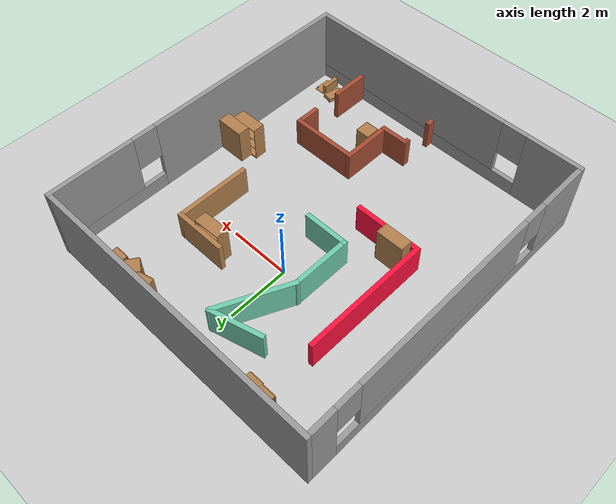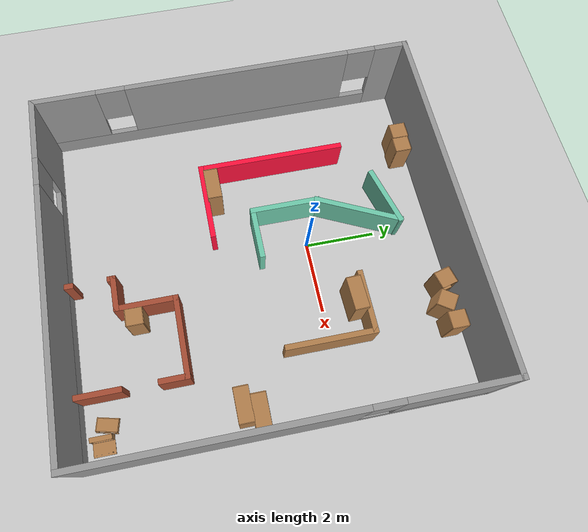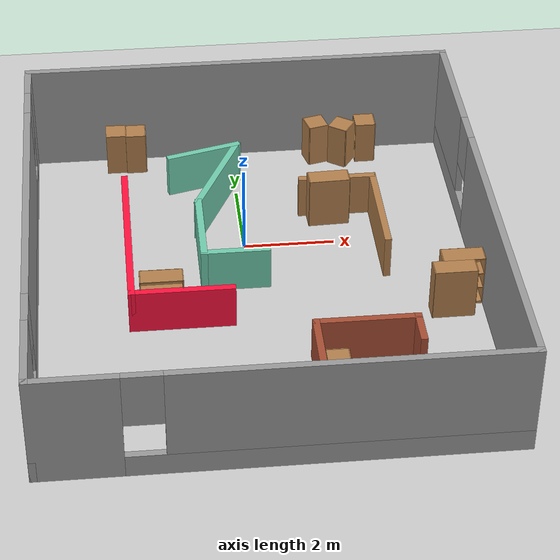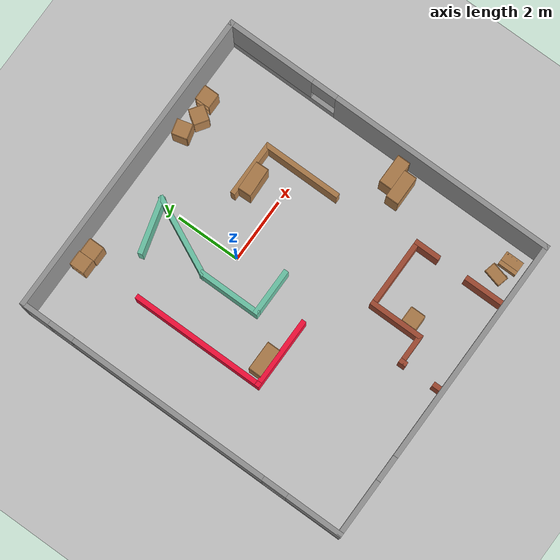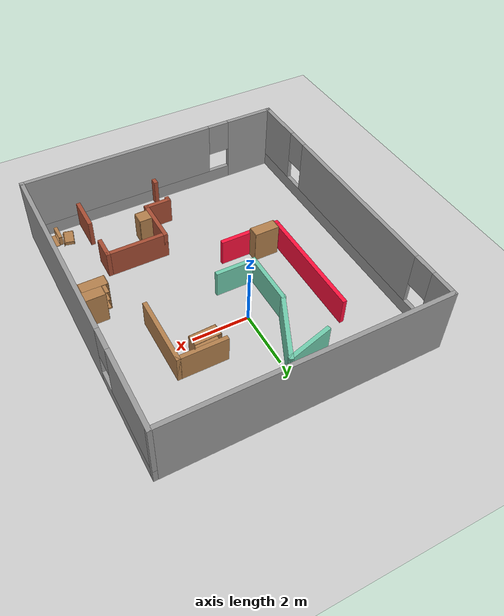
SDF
<sdf version="1.6">
 <world name="default">
  <light name="sun" type="directional">
   <pose>0 0 10 0 -0 0</pose>
   <diffuse>0.8 0.8 0.8 1</diffuse>
   <specular>0.2 0.2 0.2 1</specular>
   <attenuation>
    <range>1000</range>
    <constant>0.9</constant>
    <linear>0.01</linear>
    <quadratic>0.001</quadratic>
   </attenuation>
   <direction>-0.5 0.1 -0.9</direction>
  </light>
  <model name="ground_plane">
   <static>1</static>
   <link name="link">
    <collision name="collision">
     <geometry><plane><normal>0 0 1</normal><size>100 100</size></plane></geometry>
     <surface>
      <contact><collide_bitmask>65535</collide_bitmask></contact>
      <friction><ode><mu>100</mu><mu2>50</mu2></ode></friction>
     </surface>
    </collision>
    <visual name="visual">
     <cast_shadows>0</cast_shadows>
     <geometry><plane><normal>0 0 1</normal><size>100 100</size></plane></geometry>
     <material>
      <script><uri>file://media/materials/scripts/gazebo.material</uri><name>Gazebo/Grey</name></script>
     </material>
    </visual>
   </link>
  </model>
  <gravity>0 0 -9.8</gravity>
  <magnetic_field>6e-06 2.3e-05 -4.2e-05</magnetic_field>
  <atmosphere type="adiabatic"/>
  <physics name="default_physics" default="0" type="ode">
   <max_step_size>0.001</max_step_size>
   <real_time_factor>1</real_time_factor>
   <real_time_update_rate>1000</real_time_update_rate>
  </physics>
  <scene><ambient>0.4 0.4 0.4 1</ambient><background>0.7 0.7 0.7 1</background><shadows>1</shadows></scene>
  <spherical_coordinates>
   <surface_model>EARTH_WGS84</surface_model>
   <latitude_deg>0</latitude_deg>
   <longitude_deg>0</longitude_deg>
   <elevation>0</elevation>
   <heading_deg>0</heading_deg>
  </spherical_coordinates>
  <model name="rightone">
   <pose>0.16977 -1.56578 0 0 -0 0</pose>
   <link name="Wall_16">
    <collision name="Wall_16_Collision">
     <geometry><box><size>4.25 0.15 1</size></box></geometry>
     <pose>0 0 0.5 0 -0 0</pose>
    </collision>
    <visual name="Wall_16_Visual">
     <pose>0 0 0.5 0 -0 0</pose>
     <geometry><box><size>4.25 0.15 1</size></box></geometry>
     <material>
      <script><uri>file://media/materials/scripts/gazebo.material</uri><name>Gazebo/Grey</name></script>
      <ambient>1 0.0627451 0.235294 1</ambient>
     </material>
     <meta><layer>0</layer></meta>
    </visual>
    <pose>-2.73877 0.989782 0 0 0 -1.5708</pose>
   </link>
   <link name="Wall_17">
    <collision name="Wall_17_Collision">
     <geometry><box><size>2.25 0.15 1</size></box></geometry>
     <pose>0 0 0.5 0 -0 0</pose>
    </collision>
    <visual name="Wall_17_Visual">
     <pose>0 0 0.5 0 -0 0</pose>
     <geometry><box><size>2.25 0.15 1</size></box></geometry>
     <material>
      <script><uri>file://media/materials/scripts/gazebo.material</uri><name>Gazebo/Grey</name></script>
      <ambient>1 0.0627451 0.235294 1</ambient>
     </material>
     <meta><layer>0</layer></meta>
    </visual>
    <pose>-1.68877 -1.06022 0 0 -0 0</pose>
   </link>
   <link name="Wall_20">
    <collision name="Wall_20_Collision">
     <geometry><box><size>1.75 0.15 1</size></box></geometry>
     <pose>0 0 0.5 0 -0 0</pose>
    </collision>
    <visual name="Wall_20_Visual">
     <pose>0 0 0.5 0 -0 0</pose>
     <geometry><box><size>1.75 0.15 1</size></box></geometry>
     <material>
      <script><uri>file://media/materials/scripts/gazebo.material</uri><name>Gazebo/Grey</name></script>
      <ambient>0.435294 0.796078 0.67451 1</ambient>
     </material>
     <meta><layer>0</layer></meta>
    </visual>
    <pose>-0.890549 3.96314 0 0 -0 0.261799</pose>
   </link>
   <link name="Wall_21">
    <collision name="Wall_21_Collision">
     <geometry><box><size>2.53984 0.15 1</size></box></geometry>
     <pose>0 0 0.5 0 -0 0</pose>
    </collision>
    <visual name="Wall_21_Visual">
     <pose>0 0 0.5 0 -0 0</pose>
     <geometry><box><size>2.53984 0.15 1</size></box></geometry>
     <material>
      <script><uri>file://media/materials/scripts/gazebo.material</uri><name>Gazebo/Grey</name></script>
      <ambient>0.435294 0.796078 0.67451 1</ambient>
     </material>
     <meta><layer>0</layer></meta>
    </visual>
    <pose>-0.630789 3.09099 0 0 0 -2.01452</pose>
   </link>
   <link name="Wall_22">
    <collision name="Wall_22_Collision">
     <geometry><box><size>2 0.15 1</size></box></geometry>
     <pose>0 0 0.5 0 -0 0</pose>
    </collision>
    <visual name="Wall_22_Visual">
     <pose>0 0 0.5 0 -0 0</pose>
     <geometry><box><size>2 0.15 1</size></box></geometry>
     <material>
      <script><uri>file://media/materials/scripts/gazebo.material</uri><name>Gazebo/Grey</name></script>
      <ambient>0.435294 0.796078 0.67451 1</ambient>
     </material>
     <meta><layer>0</layer></meta>
    </visual>
    <pose>-1.14377 1.08678 0 0 0 -1.5708</pose>
   </link>
   <link name="Wall_23">
    <collision name="Wall_23_Collision">
     <geometry><box><size>1.5 0.15 1</size></box></geometry>
     <pose>0 0 0.5 0 -0 0</pose>
    </collision>
    <visual name="Wall_23_Visual">
     <pose>0 0 0.5 0 -0 0</pose>
     <geometry><box><size>1.5 0.15 1</size></box></geometry>
     <material>
      <script><uri>file://media/materials/scripts/gazebo.material</uri><name>Gazebo/Grey</name></script>
      <ambient>0.435294 0.796078 0.67451 1</ambient>
     </material>
     <meta><layer>0</layer></meta>
    </visual>
    <pose>-0.468771 0.161782 0 0 -0 0</pose>
   </link>
   <link name="Wall_25">
    <collision name="Wall_25_Collision">
     <geometry><box><size>1.75 0.15 1</size></box></geometry>
     <pose>0 0 0.5 0 -0 0</pose>
    </collision>
    <visual name="Wall_25_Visual">
     <pose>0 0 0.5 0 -0 0</pose>
     <geometry><box><size>1.75 0.15 1</size></box></geometry>
     <material>
      <script><uri>file://media/materials/scripts/gazebo.material</uri><name>Gazebo/Wood</name></script>
      <ambient>1 1 1 1</ambient>
     </material>
     <meta><layer>0</layer></meta>
    </visual>
    <pose>2.02823 2.65378 0 0 -0 0</pose>
   </link>
   <link name="Wall_26">
    <collision name="Wall_26_Collision">
     <geometry><box><size>2.5 0.15 1</size></box></geometry>
     <pose>0 0 0.5 0 -0 0</pose>
    </collision>
    <visual name="Wall_26_Visual">
     <pose>0 0 0.5 0 -0 0</pose>
     <geometry><box><size>2.5 0.15 1</size></box></geometry>
     <material>
      <script><uri>file://media/materials/scripts/gazebo.material</uri><name>Gazebo/Wood</name></script>
      <ambient>1 1 1 1</ambient>
     </material>
     <meta><layer>0</layer></meta>
    </visual>
    <pose>2.82823 1.47878 0 0 0 -1.5708</pose>
   </link>
   <link name="Wall_28">
    <pose>0.109229 -4.59822 0 0 -0 1.5708</pose>
    <visual name="Wall_28_Visual_0">
     <pose>-0.567304 0 0.5 0 -0 0</pose>
     <geometry><box><size>0.379084 0.15 1</size></box></geometry>
     <material>
      <script><uri>file://media/materials/scripts/gazebo.material</uri><name>Gazebo/Bricks</name></script>
      <ambient>1 1 1 1</ambient>
     </material>
     <meta><layer>0</layer></meta>
    </visual>
    <collision name="Wall_28_Collision_0">
     <geometry><box><size>0.379084 0.15 1</size></box></geometry>
     <pose>-0.567304 0 0.5 0 -0 0</pose>
    </collision>
    <visual name="Wall_28_Visual_1">
     <pose>0.639542 0 0.5 0 -0 0</pose>
     <geometry><box><size>0.234608 0.15 1</size></box></geometry>
     <material>
      <script><uri>file://media/materials/scripts/gazebo.material</uri><name>Gazebo/Bricks</name></script>
      <ambient>1 1 1 1</ambient>
     </material>
     <meta><layer>0</layer></meta>
    </visual>
    <collision name="Wall_28_Collision_1">
     <geometry><box><size>0.234608 0.15 1</size></box></geometry>
     <pose>0.639542 0 0.5 0 -0 0</pose>
    </collision>
   </link>
   <link name="Wall_29">
    <collision name="Wall_29_Collision">
     <geometry><box><size>1 0.15 1</size></box></geometry>
     <pose>0 0 0.5 0 -0 0</pose>
    </collision>
    <visual name="Wall_29_Visual">
     <pose>0 0 0.5 0 -0 0</pose>
     <geometry><box><size>1 0.15 1</size></box></geometry>
     <material>
      <script><uri>file://media/materials/scripts/gazebo.material</uri><name>Gazebo/Bricks</name></script>
      <ambient>1 1 1 1</ambient>
     </material>
     <meta><layer>0</layer></meta>
    </visual>
    <pose>0.534229 -3.91622 0 0 -0 0</pose>
   </link>
   <link name="Wall_3">
    <pose>-4.8 0 0 0 0 -1.5708</pose>
    <visual name="Wall_3_Visual_0">
     <pose>-4.89136 0 1.25 0 -0 0</pose>
     <geometry><box><size>0.967284 0.15 2.5</size></box></geometry>
     <material>
      <script><uri>file://media/materials/scripts/gazebo.material</uri><name>Gazebo/Grey</name></script>
      <ambient>1 1 1 1</ambient>
     </material>
     <meta><layer>0</layer></meta>
    </visual>
    <collision name="Wall_3_Collision_0">
     <geometry><box><size>0.967284 0.15 2.5</size></box></geometry>
     <pose>-4.89136 0 1.25 0 -0 0</pose>
    </collision>
    <visual name="Wall_3_Visual_1">
     <pose>0.483642 0 0.25 0 -0 0</pose>
     <geometry><box><size>9.78272 0.15 0.5</size></box></geometry>
     <material>
      <script><uri>file://media/materials/scripts/gazebo.material</uri><name>Gazebo/Grey</name></script>
      <ambient>1 1 1 1</ambient>
     </material>
     <meta><layer>0</layer></meta>
    </visual>
    <collision name="Wall_3_Collision_1">
     <geometry><box><size>9.78272 0.15 0.5</size></box></geometry>
     <pose>0.483642 0 0.25 0 -0 0</pose>
    </collision>
    <visual name="Wall_3_Visual_2">
     <pose>-0.429713 0 1.5 0 -0 0</pose>
     <geometry><box><size>6.35601 0.15 2</size></box></geometry>
     <material>
      <script><uri>file://media/materials/scripts/gazebo.material</uri><name>Gazebo/Grey</name></script>
      <ambient>1 1 1 1</ambient>
     </material>
     <meta><layer>0</layer></meta>
    </visual>
    <collision name="Wall_3_Collision_2">
     <geometry><box><size>6.35601 0.15 2</size></box></geometry>
     <pose>-0.429713 0 1.5 0 -0 0</pose>
    </collision>
    <visual name="Wall_3_Visual_3">
     <pose>4.46164 0 1.5 0 -0 0</pose>
     <geometry><box><size>1.82671 0.15 2</size></box></geometry>
     <material>
      <script><uri>file://media/materials/scripts/gazebo.material</uri><name>Gazebo/Grey</name></script>
      <ambient>1 1 1 1</ambient>
     </material>
     <meta><layer>0</layer></meta>
    </visual>
    <collision name="Wall_3_Collision_3">
     <geometry><box><size>1.82671 0.15 2</size></box></geometry>
     <pose>4.46164 0 1.5 0 -0 0</pose>
    </collision>
    <visual name="Wall_3_Visual_4">
     <pose>-4.00772 0 1.9 0 -0 0</pose>
     <geometry><box><size>0.8 0.15 1.2</size></box></geometry>
     <material>
      <script><uri>file://media/materials/scripts/gazebo.material</uri><name>Gazebo/Grey</name></script>
      <ambient>1 1 1 1</ambient>
     </material>
     <meta><layer>0</layer></meta>
    </visual>
    <collision name="Wall_3_Collision_4">
     <geometry><box><size>0.8 0.15 1.2</size></box></geometry>
     <pose>-4.00772 0 1.9 0 -0 0</pose>
    </collision>
    <visual name="Wall_3_Visual_5">
     <pose>3.14829 0 1.9 0 -0 0</pose>
     <geometry><box><size>0.8 0.15 1.2</size></box></geometry>
     <material>
      <script><uri>file://media/materials/scripts/gazebo.material</uri><name>Gazebo/Grey</name></script>
      <ambient>1 1 1 1</ambient>
     </material>
     <meta><layer>0</layer></meta>
    </visual>
    <collision name="Wall_3_Collision_5">
     <geometry><box><size>0.8 0.15 1.2</size></box></geometry>
     <pose>3.14829 0 1.9 0 -0 0</pose>
    </collision>
   </link>
   <link name="Wall_30">
    <collision name="Wall_30_Collision">
     <geometry><box><size>1.736 0.15 1</size></box></geometry>
     <pose>0 0 0.5 0 -0 0</pose>
    </collision>
    <visual name="Wall_30_Visual">
     <pose>0 0 0.5 0 -0 0</pose>
     <geometry><box><size>1.736 0.15 1</size></box></geometry>
     <material>
      <script><uri>file://media/materials/scripts/gazebo.material</uri><name>Gazebo/Bricks</name></script>
      <ambient>1 1 1 1</ambient>
     </material>
     <meta><layer>0</layer></meta>
    </visual>
    <pose>0.959229 -3.12322 0 0 -0 1.5708</pose>
   </link>
   <link name="Wall_31">
    <collision name="Wall_31_Collision">
     <geometry><box><size>2.25 0.15 1</size></box></geometry>
     <pose>0 0 0.5 0 -0 0</pose>
    </collision>
    <visual name="Wall_31_Visual">
     <pose>0 0 0.5 0 -0 0</pose>
     <geometry><box><size>2.25 0.15 1</size></box></geometry>
     <material>
      <script><uri>file://media/materials/scripts/gazebo.material</uri><name>Gazebo/Bricks</name></script>
      <ambient>1 1 1 1</ambient>
     </material>
     <meta><layer>0</layer></meta>
    </visual>
    <pose>2.00923 -2.33022 0 0 -0 0</pose>
   </link>
   <link name="Wall_32">
    <pose>3.05923 -3.75522 0 0 0 -1.5708</pose>
    <visual name="Wall_32_Visual_0">
     <pose>-1.08452 0 0.5 0 -0 0</pose>
     <geometry><box><size>0.830966 0.15 1</size></box></geometry>
     <material>
      <script><uri>file://media/materials/scripts/gazebo.material</uri><name>Gazebo/Bricks</name></script>
      <ambient>1 1 1 1</ambient>
     </material>
     <meta><layer>0</layer></meta>
    </visual>
    <collision name="Wall_32_Collision_0">
     <geometry><box><size>0.830966 0.15 1</size></box></geometry>
     <pose>-1.08452 0 0.5 0 -0 0</pose>
    </collision>
    <visual name="Wall_32_Visual_1">
     <pose>0.865483 0 0.5 0 -0 0</pose>
     <geometry><box><size>1.26903 0.15 1</size></box></geometry>
     <material>
      <script><uri>file://media/materials/scripts/gazebo.material</uri><name>Gazebo/Bricks</name></script>
      <ambient>1 1 1 1</ambient>
     </material>
     <meta><layer>0</layer></meta>
    </visual>
    <collision name="Wall_32_Collision_1">
     <geometry><box><size>1.26903 0.15 1</size></box></geometry>
     <pose>0.865483 0 0.5 0 -0 0</pose>
    </collision>
   </link>
   <link name="Wall_4">
    <pose>0 -5.3 0 0 -0 0</pose>
    <visual name="Wall_4_Visual_0">
     <pose>-3.95911 0 1.25 0 -0 0</pose>
     <geometry><box><size>1.83179 0.15 2.5</size></box></geometry>
     <material>
      <script><uri>file://media/materials/scripts/gazebo.material</uri><name>Gazebo/Grey</name></script>
      <ambient>1 1 1 1</ambient>
     </material>
     <meta><layer>0</layer></meta>
    </visual>
    <collision name="Wall_4_Collision_0">
     <geometry><box><size>1.83179 0.15 2.5</size></box></geometry>
     <pose>-3.95911 0 1.25 0 -0 0</pose>
    </collision>
    <visual name="Wall_4_Visual_1">
     <pose>0.915894 0 0.25 0 -0 0</pose>
     <geometry><box><size>7.91821 0.15 0.5</size></box></geometry>
     <material>
      <script><uri>file://media/materials/scripts/gazebo.material</uri><name>Gazebo/Grey</name></script>
      <ambient>1 1 1 1</ambient>
     </material>
     <meta><layer>0</layer></meta>
    </visual>
    <collision name="Wall_4_Collision_1">
     <geometry><box><size>7.91821 0.15 0.5</size></box></geometry>
     <pose>0.915894 0 0.25 0 -0 0</pose>
    </collision>
    <visual name="Wall_4_Visual_2">
     <pose>1.31589 0 1.5 0 -0 0</pose>
     <geometry><box><size>7.11821 0.15 2</size></box></geometry>
     <material>
      <script><uri>file://media/materials/scripts/gazebo.material</uri><name>Gazebo/Grey</name></script>
      <ambient>1 1 1 1</ambient>
     </material>
     <meta><layer>0</layer></meta>
    </visual>
    <collision name="Wall_4_Collision_2">
     <geometry><box><size>7.11821 0.15 2</size></box></geometry>
     <pose>1.31589 0 1.5 0 -0 0</pose>
    </collision>
    <visual name="Wall_4_Visual_3">
     <pose>-2.64321 0 1.9 0 -0 0</pose>
     <geometry><box><size>0.8 0.15 1.2</size></box></geometry>
     <material>
      <script><uri>file://media/materials/scripts/gazebo.material</uri><name>Gazebo/Grey</name></script>
      <ambient>1 1 1 1</ambient>
     </material>
     <meta><layer>0</layer></meta>
    </visual>
    <collision name="Wall_4_Collision_3">
     <geometry><box><size>0.8 0.15 1.2</size></box></geometry>
     <pose>-2.64321 0 1.9 0 -0 0</pose>
    </collision>
   </link>
   <link name="Wall_5">
    <pose>4.8 0 0 0 -0 1.5708</pose>
    <visual name="Wall_5_Visual_0">
     <pose>-1.8194 0 1.25 0 -0 0</pose>
     <geometry><box><size>7.11119 0.15 2.5</size></box></geometry>
     <material>
      <script><uri>file://media/materials/scripts/gazebo.material</uri><name>Gazebo/Grey</name></script>
      <ambient>1 1 1 1</ambient>
     </material>
     <meta><layer>0</layer></meta>
    </visual>
    <collision name="Wall_5_Collision_0">
     <geometry><box><size>7.11119 0.15 2.5</size></box></geometry>
     <pose>-1.8194 0 1.25 0 -0 0</pose>
    </collision>
    <visual name="Wall_5_Visual_1">
     <pose>3.5556 0 0.25 0 -0 0</pose>
     <geometry><box><size>3.63881 0.15 0.5</size></box></geometry>
     <material>
      <script><uri>file://media/materials/scripts/gazebo.material</uri><name>Gazebo/Grey</name></script>
      <ambient>1 1 1 1</ambient>
     </material>
     <meta><layer>0</layer></meta>
    </visual>
    <collision name="Wall_5_Collision_1">
     <geometry><box><size>3.63881 0.15 0.5</size></box></geometry>
     <pose>3.5556 0 0.25 0 -0 0</pose>
    </collision>
    <visual name="Wall_5_Visual_2">
     <pose>3.9556 0 1.5 0 -0 0</pose>
     <geometry><box><size>2.83881 0.15 2</size></box></geometry>
     <material>
      <script><uri>file://media/materials/scripts/gazebo.material</uri><name>Gazebo/Grey</name></script>
      <ambient>1 1 1 1</ambient>
     </material>
     <meta><layer>0</layer></meta>
    </visual>
    <collision name="Wall_5_Collision_2">
     <geometry><box><size>2.83881 0.15 2</size></box></geometry>
     <pose>3.9556 0 1.5 0 -0 0</pose>
    </collision>
    <visual name="Wall_5_Visual_3">
     <pose>2.13619 0 1.9 0 -0 0</pose>
     <geometry><box><size>0.8 0.15 1.2</size></box></geometry>
     <material>
      <script><uri>file://media/materials/scripts/gazebo.material</uri><name>Gazebo/Grey</name></script>
      <ambient>1 1 1 1</ambient>
     </material>
     <meta><layer>0</layer></meta>
    </visual>
    <collision name="Wall_5_Collision_3">
     <geometry><box><size>0.8 0.15 1.2</size></box></geometry>
     <pose>2.13619 0 1.9 0 -0 0</pose>
    </collision>
   </link>
   <link name="Wall_6">
    <collision name="Wall_6_Collision">
     <geometry><box><size>9.75 0.15 2.5</size></box></geometry>
     <pose>0 0 1.25 0 -0 0</pose>
    </collision>
    <visual name="Wall_6_Visual">
     <pose>0 0 1.25 0 -0 0</pose>
     <geometry><box><size>9.75 0.15 2.5</size></box></geometry>
     <material>
      <script><uri>file://media/materials/scripts/gazebo.material</uri><name>Gazebo/Grey</name></script>
      <ambient>1 1 1 1</ambient>
     </material>
     <meta><layer>0</layer></meta>
    </visual>
    <pose>0 5.3 0 0 -0 3.14159</pose>
   </link>
   <static>1</static>
  </model>
  <model name="bookshelf">
   <static>1</static>
   <link name="link">
    <inertial><mass>1</mass></inertial>
    <collision name="back">
     <pose>0 0.005 0.6 0 -0 0</pose>
     <geometry><box><size>0.9 0.01 1.2</size></box></geometry>
    </collision>
    <visual name="visual1">
     <pose>0 0.005 0.6 0 -0 0</pose>
     <geometry><box><size>0.9 0.01 1.2</size></box></geometry>
     <material>
      <script><uri>file://media/materials/scripts/gazebo.material</uri><name>Gazebo/Wood</name></script>
     </material>
    </visual>
    <collision name="left_side">
     <pose>0.45 -0.195 0.6 0 -0 0</pose>
     <geometry><box><size>0.02 0.4 1.2</size></box></geometry>
    </collision>
    <visual name="visual2">
     <pose>0.45 -0.195 0.6 0 -0 0</pose>
     <geometry><box><size>0.02 0.4 1.2</size></box></geometry>
     <material>
      <script><uri>file://media/materials/scripts/gazebo.material</uri><name>Gazebo/Wood</name></script>
     </material>
    </visual>
    <collision name="right_side">
     <pose>-0.45 -0.195 0.6 0 -0 0</pose>
     <geometry><box><size>0.02 0.4 1.2</size></box></geometry>
    </collision>
    <visual name="visual3">
     <pose>-0.45 -0.195 0.6 0 -0 0</pose>
     <geometry><box><size>0.02 0.4 1.2</size></box></geometry>
     <material>
      <script><uri>file://media/materials/scripts/gazebo.material</uri><name>Gazebo/Wood</name></script>
     </material>
    </visual>
    <collision name="bottom">
     <pose>0 -0.195 0.03 0 -0 0</pose>
     <geometry><box><size>0.88 0.4 0.06</size></box></geometry>
    </collision>
    <visual name="visual4">
     <pose>0 -0.195 0.03 0 -0 0</pose>
     <geometry><box><size>0.88 0.4 0.06</size></box></geometry>
     <material>
      <script><uri>file://media/materials/scripts/gazebo.material</uri><name>Gazebo/Wood</name></script>
     </material>
    </visual>
    <collision name="top">
     <pose>0 -0.195 1.19 0 -0 0</pose>
     <geometry><box><size>0.88 0.4 0.02</size></box></geometry>
    </collision>
    <visual name="visual5">
     <pose>0 -0.195 1.19 0 -0 0</pose>
     <geometry><box><size>0.88 0.4 0.02</size></box></geometry>
     <material>
      <script><uri>file://media/materials/scripts/gazebo.material</uri><name>Gazebo/Wood</name></script>
     </material>
    </visual>
    <collision name="low_shelf">
     <pose>0 -0.195 0.43 0 -0 0</pose>
     <geometry><box><size>0.88 0.4 0.02</size></box></geometry>
    </collision>
    <visual name="visual6">
     <pose>0 -0.195 0.43 0 -0 0</pose>
     <geometry><box><size>0.88 0.4 0.02</size></box></geometry>
     <material>
      <script><uri>file://media/materials/scripts/gazebo.material</uri><name>Gazebo/Wood</name></script>
     </material>
    </visual>
    <collision name="high_shelf">
     <pose>0 -0.195 0.8 0 -0 0</pose>
     <geometry><box><size>0.88 0.4 0.02</size></box></geometry>
    </collision>
    <visual name="visual7">
     <pose>0 -0.195 0.8 0 -0 0</pose>
     <geometry><box><size>0.88 0.4 0.02</size></box></geometry>
     <material>
      <script><uri>file://media/materials/scripts/gazebo.material</uri><name>Gazebo/Wood</name></script>
     </material>
    </visual>
   </link>
   <pose>4.43633 -2.04794 0 0 -0 0</pose>
  </model>
  <model name="bookshelf_0">
   <static>1</static>
   <link name="link">
    <inertial><mass>1</mass></inertial>
    <collision name="back">
     <pose>0 0.005 0.6 0 -0 0</pose>
     <geometry><box><size>0.9 0.01 1.2</size></box></geometry>
    </collision>
    <visual name="visual1">
     <pose>0 0.005 0.6 0 -0 0</pose>
     <geometry><box><size>0.9 0.01 1.2</size></box></geometry>
     <material>
      <script><uri>file://media/materials/scripts/gazebo.material</uri><name>Gazebo/Wood</name></script>
     </material>
    </visual>
    <collision name="left_side">
     <pose>0.45 -0.195 0.6 0 -0 0</pose>
     <geometry><box><size>0.02 0.4 1.2</size></box></geometry>
    </collision>
    <visual name="visual2">
     <pose>0.45 -0.195 0.6 0 -0 0</pose>
     <geometry><box><size>0.02 0.4 1.2</size></box></geometry>
     <material>
      <script><uri>file://media/materials/scripts/gazebo.material</uri><name>Gazebo/Wood</name></script>
     </material>
    </visual>
    <collision name="right_side">
     <pose>-0.45 -0.195 0.6 0 -0 0</pose>
     <geometry><box><size>0.02 0.4 1.2</size></box></geometry>
    </collision>
    <visual name="visual3">
     <pose>-0.45 -0.195 0.6 0 -0 0</pose>
     <geometry><box><size>0.02 0.4 1.2</size></box></geometry>
     <material>
      <script><uri>file://media/materials/scripts/gazebo.material</uri><name>Gazebo/Wood</name></script>
     </material>
    </visual>
    <collision name="bottom">
     <pose>0 -0.195 0.03 0 -0 0</pose>
     <geometry><box><size>0.88 0.4 0.06</size></box></geometry>
    </collision>
    <visual name="visual4">
     <pose>0 -0.195 0.03 0 -0 0</pose>
     <geometry><box><size>0.88 0.4 0.06</size></box></geometry>
     <material>
      <script><uri>file://media/materials/scripts/gazebo.material</uri><name>Gazebo/Wood</name></script>
     </material>
    </visual>
    <collision name="top">
     <pose>0 -0.195 1.19 0 -0 0</pose>
     <geometry><box><size>0.88 0.4 0.02</size></box></geometry>
    </collision>
    <visual name="visual5">
     <pose>0 -0.195 1.19 0 -0 0</pose>
     <geometry><box><size>0.88 0.4 0.02</size></box></geometry>
     <material>
      <script><uri>file://media/materials/scripts/gazebo.material</uri><name>Gazebo/Wood</name></script>
     </material>
    </visual>
    <collision name="low_shelf">
     <pose>0 -0.195 0.43 0 -0 0</pose>
     <geometry><box><size>0.88 0.4 0.02</size></box></geometry>
    </collision>
    <visual name="visual6">
     <pose>0 -0.195 0.43 0 -0 0</pose>
     <geometry><box><size>0.88 0.4 0.02</size></box></geometry>
     <material>
      <script><uri>file://media/materials/scripts/gazebo.material</uri><name>Gazebo/Wood</name></script>
     </material>
    </visual>
    <collision name="high_shelf">
     <pose>0 -0.195 0.8 0 -0 0</pose>
     <geometry><box><size>0.88 0.4 0.02</size></box></geometry>
    </collision>
    <visual name="visual7">
     <pose>0 -0.195 0.8 0 -0 0</pose>
     <geometry><box><size>0.88 0.4 0.02</size></box></geometry>
     <material>
      <script><uri>file://media/materials/scripts/gazebo.material</uri><name>Gazebo/Wood</name></script>
     </material>
    </visual>
   </link>
   <pose>4.20146 -2.83011 0 0 0 -3.13439</pose>
  </model>
  <model name="cabinet">
   <static>1</static>
   <link name="cabinet_bottom_plate">
    <inertial>
     <pose>0 0 -1 0 -0 0</pose>
     <inertia><ixx>2.05</ixx><ixy>0</ixy><ixz>0</ixz><iyy>2.05</iyy><iyz>0</iyz><izz>2.05</izz></inertia>
     <mass>25</mass>
    </inertial>
    <collision name="cabinet_bottom_plate_geom">
     <pose>0 0 0.01 0 -0 0</pose>
     <geometry><box><size>0.45 0.45 0.02</size></box></geometry>
    </collision>
    <visual name="cabinet_bottom_plate_geom_visual">
     <pose>0 0 0.01 0 -0 0</pose>
     <geometry><box><size>0.45 0.45 0.02</size></box></geometry>
     <material>
      <script><uri>file://media/materials/scripts/gazebo.material</uri><name>Gazebo/Wood</name></script>
     </material>
    </visual>
    <collision name="cabinet_bottom_plate_geom_cabinet_back_plate">
     <pose>0.235 0 0.51 0 -0 0</pose>
     <geometry><box><size>0.02 0.45 1.02</size></box></geometry>
    </collision>
    <visual name="cabinet_bottom_plate_geom_cabinet_back_plate_visual">
     <pose>0.235 0 0.51 0 -0 0</pose>
     <geometry><box><size>0.02 0.45 1.02</size></box></geometry>
     <material>
      <script><uri>file://media/materials/scripts/gazebo.material</uri><name>Gazebo/Wood</name></script>
     </material>
    </visual>
    <collision name="cabinet_bottom_plate_geom_cabinet_left_plate">
     <pose>0 0.235 0.51 0 -0 0</pose>
     <geometry><box><size>0.45 0.02 1.02</size></box></geometry>
    </collision>
    <visual name="cabinet_bottom_plate_geom_cabinet_left_plate_visual">
     <pose>0 0.235 0.51 0 -0 0</pose>
     <geometry><box><size>0.45 0.02 1.02</size></box></geometry>
     <material>
      <script><uri>file://media/materials/scripts/gazebo.material</uri><name>Gazebo/Wood</name></script>
     </material>
    </visual>
    <collision name="cabinet_bottom_plate_geom_cabinet_middle_plate">
     <pose>0 0 0.51 0 -0 0</pose>
     <geometry><box><size>0.45 0.45 0.02</size></box></geometry>
    </collision>
    <visual name="cabinet_bottom_plate_geom_cabinet_middle_plate_visual">
     <pose>0 0 0.51 0 -0 0</pose>
     <geometry><box><size>0.45 0.45 0.02</size></box></geometry>
     <material>
      <script><uri>file://media/materials/scripts/gazebo.material</uri><name>Gazebo/Wood</name></script>
     </material>
    </visual>
    <collision name="cabinet_bottom_plate_geom_cabinet_right_plate">
     <pose>0 -0.235 0.51 0 -0 0</pose>
     <geometry><box><size>0.45 0.02 1.02</size></box></geometry>
    </collision>
    <visual name="cabinet_bottom_plate_geom_cabinet_right_plate_visual">
     <pose>0 -0.235 0.51 0 -0 0</pose>
     <geometry><box><size>0.45 0.02 1.02</size></box></geometry>
     <material>
      <script><uri>file://media/materials/scripts/gazebo.material</uri><name>Gazebo/Wood</name></script>
     </material>
    </visual>
    <collision name="cabinet_bottom_plate_geom_cabinet_top_plate">
     <pose>0 0 1.01 0 -0 0</pose>
     <geometry><box><size>0.45 0.45 0.02</size></box></geometry>
    </collision>
    <visual name="cabinet_bottom_plate_geom_cabinet_top_plate_visual">
     <pose>0 0 1.01 0 -0 0</pose>
     <geometry><box><size>0.45 0.45 0.02</size></box></geometry>
     <material>
      <script><uri>file://media/materials/scripts/gazebo.material</uri><name>Gazebo/Wood</name></script>
     </material>
    </visual>
   </link>
   <pose>1.43633 -5.04516 0 0 -0 0</pose>
  </model>
  <model name="cabinet_0">
   <static>1</static>
   <link name="cabinet_bottom_plate">
    <inertial>
     <pose>0 0 -1 0 -0 0</pose>
     <inertia><ixx>2.05</ixx><ixy>0</ixy><ixz>0</ixz><iyy>2.05</iyy><iyz>0</iyz><izz>2.05</izz></inertia>
     <mass>25</mass>
    </inertial>
    <collision name="cabinet_bottom_plate_geom">
     <pose>0 0 0.01 0 -0 0</pose>
     <geometry><box><size>0.45 0.45 0.02</size></box></geometry>
    </collision>
    <visual name="cabinet_bottom_plate_geom_visual">
     <pose>0 0 0.01 0 -0 0</pose>
     <geometry><box><size>0.45 0.45 0.02</size></box></geometry>
     <material>
      <script><uri>file://media/materials/scripts/gazebo.material</uri><name>Gazebo/Wood</name></script>
     </material>
    </visual>
    <collision name="cabinet_bottom_plate_geom_cabinet_back_plate">
     <pose>0.235 0 0.51 0 -0 0</pose>
     <geometry><box><size>0.02 0.45 1.02</size></box></geometry>
    </collision>
    <visual name="cabinet_bottom_plate_geom_cabinet_back_plate_visual">
     <pose>0.235 0 0.51 0 -0 0</pose>
     <geometry><box><size>0.02 0.45 1.02</size></box></geometry>
     <material>
      <script><uri>file://media/materials/scripts/gazebo.material</uri><name>Gazebo/Wood</name></script>
     </material>
    </visual>
    <collision name="cabinet_bottom_plate_geom_cabinet_left_plate">
     <pose>0 0.235 0.51 0 -0 0</pose>
     <geometry><box><size>0.45 0.02 1.02</size></box></geometry>
    </collision>
    <visual name="cabinet_bottom_plate_geom_cabinet_left_plate_visual">
     <pose>0 0.235 0.51 0 -0 0</pose>
     <geometry><box><size>0.45 0.02 1.02</size></box></geometry>
     <material>
      <script><uri>file://media/materials/scripts/gazebo.material</uri><name>Gazebo/Wood</name></script>
     </material>
    </visual>
    <collision name="cabinet_bottom_plate_geom_cabinet_middle_plate">
     <pose>0 0 0.51 0 -0 0</pose>
     <geometry><box><size>0.45 0.45 0.02</size></box></geometry>
    </collision>
    <visual name="cabinet_bottom_plate_geom_cabinet_middle_plate_visual">
     <pose>0 0 0.51 0 -0 0</pose>
     <geometry><box><size>0.45 0.45 0.02</size></box></geometry>
     <material>
      <script><uri>file://media/materials/scripts/gazebo.material</uri><name>Gazebo/Wood</name></script>
     </material>
    </visual>
    <collision name="cabinet_bottom_plate_geom_cabinet_right_plate">
     <pose>0 -0.235 0.51 0 -0 0</pose>
     <geometry><box><size>0.45 0.02 1.02</size></box></geometry>
    </collision>
    <visual name="cabinet_bottom_plate_geom_cabinet_right_plate_visual">
     <pose>0 -0.235 0.51 0 -0 0</pose>
     <geometry><box><size>0.45 0.02 1.02</size></box></geometry>
     <material>
      <script><uri>file://media/materials/scripts/gazebo.material</uri><name>Gazebo/Wood</name></script>
     </material>
    </visual>
    <collision name="cabinet_bottom_plate_geom_cabinet_top_plate">
     <pose>0 0 1.01 0 -0 0</pose>
     <geometry><box><size>0.45 0.45 0.02</size></box></geometry>
    </collision>
    <visual name="cabinet_bottom_plate_geom_cabinet_top_plate_visual">
     <pose>0 0 1.01 0 -0 0</pose>
     <geometry><box><size>0.45 0.45 0.02</size></box></geometry>
     <material>
      <script><uri>file://media/materials/scripts/gazebo.material</uri><name>Gazebo/Wood</name></script>
     </material>
    </visual>
   </link>
   <pose>3.11683 3.28614 0 0 -0 0</pose>
  </model>
  <model name="cabinet_1">
   <static>1</static>
   <link name="cabinet_bottom_plate">
    <inertial>
     <pose>0 0 -1 0 -0 0</pose>
     <inertia><ixx>2.05</ixx><ixy>0</ixy><ixz>0</ixz><iyy>2.05</iyy><iyz>0</iyz><izz>2.05</izz></inertia>
     <mass>25</mass>
    </inertial>
    <collision name="cabinet_bottom_plate_geom">
     <pose>0 0 0.01 0 -0 0</pose>
     <geometry><box><size>0.45 0.45 0.02</size></box></geometry>
    </collision>
    <visual name="cabinet_bottom_plate_geom_visual">
     <pose>0 0 0.01 0 -0 0</pose>
     <geometry><box><size>0.45 0.45 0.02</size></box></geometry>
     <material>
      <script><uri>file://media/materials/scripts/gazebo.material</uri><name>Gazebo/Wood</name></script>
     </material>
    </visual>
    <collision name="cabinet_bottom_plate_geom_cabinet_back_plate">
     <pose>0.235 0 0.51 0 -0 0</pose>
     <geometry><box><size>0.02 0.45 1.02</size></box></geometry>
    </collision>
    <visual name="cabinet_bottom_plate_geom_cabinet_back_plate_visual">
     <pose>0.235 0 0.51 0 -0 0</pose>
     <geometry><box><size>0.02 0.45 1.02</size></box></geometry>
     <material>
      <script><uri>file://media/materials/scripts/gazebo.material</uri><name>Gazebo/Wood</name></script>
     </material>
    </visual>
    <collision name="cabinet_bottom_plate_geom_cabinet_left_plate">
     <pose>0 0.235 0.51 0 -0 0</pose>
     <geometry><box><size>0.45 0.02 1.02</size></box></geometry>
    </collision>
    <visual name="cabinet_bottom_plate_geom_cabinet_left_plate_visual">
     <pose>0 0.235 0.51 0 -0 0</pose>
     <geometry><box><size>0.45 0.02 1.02</size></box></geometry>
     <material>
      <script><uri>file://media/materials/scripts/gazebo.material</uri><name>Gazebo/Wood</name></script>
     </material>
    </visual>
    <collision name="cabinet_bottom_plate_geom_cabinet_middle_plate">
     <pose>0 0 0.51 0 -0 0</pose>
     <geometry><box><size>0.45 0.45 0.02</size></box></geometry>
    </collision>
    <visual name="cabinet_bottom_plate_geom_cabinet_middle_plate_visual">
     <pose>0 0 0.51 0 -0 0</pose>
     <geometry><box><size>0.45 0.45 0.02</size></box></geometry>
     <material>
      <script><uri>file://media/materials/scripts/gazebo.material</uri><name>Gazebo/Wood</name></script>
     </material>
    </visual>
    <collision name="cabinet_bottom_plate_geom_cabinet_right_plate">
     <pose>0 -0.235 0.51 0 -0 0</pose>
     <geometry><box><size>0.45 0.02 1.02</size></box></geometry>
    </collision>
    <visual name="cabinet_bottom_plate_geom_cabinet_right_plate_visual">
     <pose>0 -0.235 0.51 0 -0 0</pose>
     <geometry><box><size>0.45 0.02 1.02</size></box></geometry>
     <material>
      <script><uri>file://media/materials/scripts/gazebo.material</uri><name>Gazebo/Wood</name></script>
     </material>
    </visual>
    <collision name="cabinet_bottom_plate_geom_cabinet_top_plate">
     <pose>0 0 1.01 0 -0 0</pose>
     <geometry><box><size>0.45 0.45 0.02</size></box></geometry>
    </collision>
    <visual name="cabinet_bottom_plate_geom_cabinet_top_plate_visual">
     <pose>0 0 1.01 0 -0 0</pose>
     <geometry><box><size>0.45 0.45 0.02</size></box></geometry>
     <material>
      <script><uri>file://media/materials/scripts/gazebo.material</uri><name>Gazebo/Wood</name></script>
     </material>
    </visual>
   </link>
   <pose>2.56628 3.16563 0 0 0 -0.590228</pose>
  </model>
  <model name="cabinet_2">
   <static>1</static>
   <link name="cabinet_bottom_plate">
    <inertial>
     <pose>0 0 -1 0 -0 0</pose>
     <inertia><ixx>2.05</ixx><ixy>0</ixy><ixz>0</ixz><iyy>2.05</iyy><iyz>0</iyz><izz>2.05</izz></inertia>
     <mass>25</mass>
    </inertial>
    <collision name="cabinet_bottom_plate_geom">
     <pose>0 0 0.01 0 -0 0</pose>
     <geometry><box><size>0.45 0.45 0.02</size></box></geometry>
    </collision>
    <visual name="cabinet_bottom_plate_geom_visual">
     <pose>0 0 0.01 0 -0 0</pose>
     <geometry><box><size>0.45 0.45 0.02</size></box></geometry>
     <material>
      <script><uri>file://media/materials/scripts/gazebo.material</uri><name>Gazebo/Wood</name></script>
     </material>
    </visual>
    <collision name="cabinet_bottom_plate_geom_cabinet_back_plate">
     <pose>0.235 0 0.51 0 -0 0</pose>
     <geometry><box><size>0.02 0.45 1.02</size></box></geometry>
    </collision>
    <visual name="cabinet_bottom_plate_geom_cabinet_back_plate_visual">
     <pose>0.235 0 0.51 0 -0 0</pose>
     <geometry><box><size>0.02 0.45 1.02</size></box></geometry>
     <material>
      <script><uri>file://media/materials/scripts/gazebo.material</uri><name>Gazebo/Wood</name></script>
     </material>
    </visual>
    <collision name="cabinet_bottom_plate_geom_cabinet_left_plate">
     <pose>0 0.235 0.51 0 -0 0</pose>
     <geometry><box><size>0.45 0.02 1.02</size></box></geometry>
    </collision>
    <visual name="cabinet_bottom_plate_geom_cabinet_left_plate_visual">
     <pose>0 0.235 0.51 0 -0 0</pose>
     <geometry><box><size>0.45 0.02 1.02</size></box></geometry>
     <material>
      <script><uri>file://media/materials/scripts/gazebo.material</uri><name>Gazebo/Wood</name></script>
     </material>
    </visual>
    <collision name="cabinet_bottom_plate_geom_cabinet_middle_plate">
     <pose>0 0 0.51 0 -0 0</pose>
     <geometry><box><size>0.45 0.45 0.02</size></box></geometry>
    </collision>
    <visual name="cabinet_bottom_plate_geom_cabinet_middle_plate_visual">
     <pose>0 0 0.51 0 -0 0</pose>
     <geometry><box><size>0.45 0.45 0.02</size></box></geometry>
     <material>
      <script><uri>file://media/materials/scripts/gazebo.material</uri><name>Gazebo/Wood</name></script>
     </material>
    </visual>
    <collision name="cabinet_bottom_plate_geom_cabinet_right_plate">
     <pose>0 -0.235 0.51 0 -0 0</pose>
     <geometry><box><size>0.45 0.02 1.02</size></box></geometry>
    </collision>
    <visual name="cabinet_bottom_plate_geom_cabinet_right_plate_visual">
     <pose>0 -0.235 0.51 0 -0 0</pose>
     <geometry><box><size>0.45 0.02 1.02</size></box></geometry>
     <material>
      <script><uri>file://media/materials/scripts/gazebo.material</uri><name>Gazebo/Wood</name></script>
     </material>
    </visual>
    <collision name="cabinet_bottom_plate_geom_cabinet_top_plate">
     <pose>0 0 1.01 0 -0 0</pose>
     <geometry><box><size>0.45 0.45 0.02</size></box></geometry>
    </collision>
    <visual name="cabinet_bottom_plate_geom_cabinet_top_plate_visual">
     <pose>0 0 1.01 0 -0 0</pose>
     <geometry><box><size>0.45 0.45 0.02</size></box></geometry>
     <material>
      <script><uri>file://media/materials/scripts/gazebo.material</uri><name>Gazebo/Wood</name></script>
     </material>
    </visual>
   </link>
   <pose>1.97382 3.30444 0 0 0 -2.89637</pose>
  </model>
  <model name="bookshelf_1">
   <static>1</static>
   <link name="link">
    <inertial><mass>1</mass></inertial>
    <collision name="back">
     <pose>0 0.005 0.6 0 -0 0</pose>
     <geometry><box><size>0.9 0.01 1.2</size></box></geometry>
    </collision>
    <visual name="visual1">
     <pose>0 0.005 0.6 0 -0 0</pose>
     <geometry><box><size>0.9 0.01 1.2</size></box></geometry>
     <material>
      <script><uri>file://media/materials/scripts/gazebo.material</uri><name>Gazebo/Wood</name></script>
     </material>
    </visual>
    <collision name="left_side">
     <pose>0.45 -0.195 0.6 0 -0 0</pose>
     <geometry><box><size>0.02 0.4 1.2</size></box></geometry>
    </collision>
    <visual name="visual2">
     <pose>0.45 -0.195 0.6 0 -0 0</pose>
     <geometry><box><size>0.02 0.4 1.2</size></box></geometry>
     <material>
      <script><uri>file://media/materials/scripts/gazebo.material</uri><name>Gazebo/Wood</name></script>
     </material>
    </visual>
    <collision name="right_side">
     <pose>-0.45 -0.195 0.6 0 -0 0</pose>
     <geometry><box><size>0.02 0.4 1.2</size></box></geometry>
    </collision>
    <visual name="visual3">
     <pose>-0.45 -0.195 0.6 0 -0 0</pose>
     <geometry><box><size>0.02 0.4 1.2</size></box></geometry>
     <material>
      <script><uri>file://media/materials/scripts/gazebo.material</uri><name>Gazebo/Wood</name></script>
     </material>
    </visual>
    <collision name="bottom">
     <pose>0 -0.195 0.03 0 -0 0</pose>
     <geometry><box><size>0.88 0.4 0.06</size></box></geometry>
    </collision>
    <visual name="visual4">
     <pose>0 -0.195 0.03 0 -0 0</pose>
     <geometry><box><size>0.88 0.4 0.06</size></box></geometry>
     <material>
      <script><uri>file://media/materials/scripts/gazebo.material</uri><name>Gazebo/Wood</name></script>
     </material>
    </visual>
    <collision name="top">
     <pose>0 -0.195 1.19 0 -0 0</pose>
     <geometry><box><size>0.88 0.4 0.02</size></box></geometry>
    </collision>
    <visual name="visual5">
     <pose>0 -0.195 1.19 0 -0 0</pose>
     <geometry><box><size>0.88 0.4 0.02</size></box></geometry>
     <material>
      <script><uri>file://media/materials/scripts/gazebo.material</uri><name>Gazebo/Wood</name></script>
     </material>
    </visual>
    <collision name="low_shelf">
     <pose>0 -0.195 0.43 0 -0 0</pose>
     <geometry><box><size>0.88 0.4 0.02</size></box></geometry>
    </collision>
    <visual name="visual6">
     <pose>0 -0.195 0.43 0 -0 0</pose>
     <geometry><box><size>0.88 0.4 0.02</size></box></geometry>
     <material>
      <script><uri>file://media/materials/scripts/gazebo.material</uri><name>Gazebo/Wood</name></script>
     </material>
    </visual>
    <collision name="high_shelf">
     <pose>0 -0.195 0.8 0 -0 0</pose>
     <geometry><box><size>0.88 0.4 0.02</size></box></geometry>
    </collision>
    <visual name="visual7">
     <pose>0 -0.195 0.8 0 -0 0</pose>
     <geometry><box><size>0.88 0.4 0.02</size></box></geometry>
     <material>
      <script><uri>file://media/materials/scripts/gazebo.material</uri><name>Gazebo/Wood</name></script>
     </material>
    </visual>
   </link>
   <pose>1.97568 0.642025 0 0 0 -3.10606</pose>
  </model>
  <model name="wooden_case_0">
   <link name="base">
    <pose>0 0 0.024 0 -0 0</pose>
    <inertial>
     <pose>-0.022184 0 0.171592 0 -0 0</pose>
     <mass>3.96264</mass>
     <inertia>
      <ixx>0.213536</ixx>
      <ixy>0</ixy>
      <ixz>0.000779377</ixz>
      <iyy>0.0708943</iyy>
      <iyz>0</iyz>
      <izz>0.154604</izz>
     </inertia>
    </inertial>
    <collision name="collision_back">
     <pose>-0.053975 0 0.1778 0 -0 0</pose>
     <geometry><box><size>0.01905 0.5461 0.3175</size></box></geometry>
     <surface>
      <contact>
       <poissons_ratio>0.347</poissons_ratio>
       <elastic_modulus>8.8e+09</elastic_modulus>
       <ode><kp>100000</kp><kd>100</kd><max_vel>100</max_vel><min_depth>0.001</min_depth></ode>
      </contact>
      <friction>
       <torsional>
        <coefficient>1</coefficient>
        <use_patch_radius>0</use_patch_radius>
        <surface_radius>0.01</surface_radius>
       </torsional>
      </friction>
     </surface>
    </collision>
    <visual name="visual_back">
     <pose>-0.053975 0 0.1778 0 -0 0</pose>
     <geometry><box><size>0.01905 0.5461 0.3175</size></box></geometry>
     <material>
      <script><uri>file://media/materials/scripts/gazebo.material</uri><name>Gazebo/Wood</name></script>
     </material>
    </visual>
    <collision name="collision_bottom">
     <pose>0 0 0.009525 0 -0 0</pose>
     <geometry><box><size>0.127 0.5842 0.01905</size></box></geometry>
     <surface>
      <contact>
       <poissons_ratio>0.347</poissons_ratio>
       <elastic_modulus>8.8e+09</elastic_modulus>
       <ode><kp>100000</kp><kd>100</kd><max_vel>100</max_vel><min_depth>0.001</min_depth></ode>
      </contact>
      <friction>
       <torsional>
        <coefficient>1</coefficient>
        <use_patch_radius>0</use_patch_radius>
        <surface_radius>0.01</surface_radius>
       </torsional>
      </friction>
     </surface>
    </collision>
    <visual name="visual_bottom">
     <pose>0 0 0.009525 0 -0 0</pose>
     <geometry><box><size>0.127 0.5842 0.01905</size></box></geometry>
     <material>
      <script><uri>file://media/materials/scripts/gazebo.material</uri><name>Gazebo/Wood</name></script>
     </material>
    </visual>
    <collision name="collision_top">
     <pose>0 0 0.346075 0 -0 0</pose>
     <geometry><box><size>0.127 0.5842 0.01905</size></box></geometry>
     <surface>
      <contact>
       <poissons_ratio>0.347</poissons_ratio>
       <elastic_modulus>8.8e+09</elastic_modulus>
       <ode><kp>100000</kp><kd>100</kd><max_vel>100</max_vel><min_depth>0.001</min_depth></ode>
      </contact>
      <friction>
       <torsional>
        <coefficient>1</coefficient>
        <use_patch_radius>0</use_patch_radius>
        <surface_radius>0.01</surface_radius>
       </torsional>
      </friction>
     </surface>
    </collision>
    <visual name="visual_top">
     <pose>0 0 0.346075 0 -0 0</pose>
     <geometry><box><size>0.127 0.5842 0.01905</size></box></geometry>
     <material>
      <script><uri>file://media/materials/scripts/gazebo.material</uri><name>Gazebo/Wood</name></script>
     </material>
    </visual>
    <collision name="collision_left">
     <pose>0 -0.282575 0.1778 0 -0 0</pose>
     <geometry><box><size>0.127 0.01905 0.3175</size></box></geometry>
     <surface>
      <contact>
       <poissons_ratio>0.347</poissons_ratio>
       <elastic_modulus>8.8e+09</elastic_modulus>
       <ode><kp>100000</kp><kd>100</kd><max_vel>100</max_vel><min_depth>0.001</min_depth></ode>
      </contact>
      <friction>
       <torsional>
        <coefficient>1</coefficient>
        <use_patch_radius>0</use_patch_radius>
        <surface_radius>0.01</surface_radius>
       </torsional>
      </friction>
     </surface>
    </collision>
    <visual name="visual_left">
     <pose>0 -0.282575 0.1778 0 -0 0</pose>
     <geometry><box><size>0.127 0.01905 0.3175</size></box></geometry>
     <material>
      <script><uri>file://media/materials/scripts/gazebo.material</uri><name>Gazebo/Wood</name></script>
     </material>
    </visual>
    <collision name="collision_right">
     <pose>0 0.282575 0.1778 0 -0 0</pose>
     <geometry><box><size>0.127 0.01905 0.3175</size></box></geometry>
     <surface>
      <contact>
       <poissons_ratio>0.347</poissons_ratio>
       <elastic_modulus>8.8e+09</elastic_modulus>
       <ode><kp>100000</kp><kd>100</kd><max_vel>100</max_vel><min_depth>0.001</min_depth></ode>
      </contact>
      <friction>
       <torsional>
        <coefficient>1</coefficient>
        <use_patch_radius>0</use_patch_radius>
        <surface_radius>0.01</surface_radius>
       </torsional>
      </friction>
     </surface>
    </collision>
    <visual name="visual_right">
     <pose>0 0.282575 0.1778 0 -0 0</pose>
     <geometry><box><size>0.127 0.01905 0.3175</size></box></geometry>
     <material>
      <script><uri>file://media/materials/scripts/gazebo.material</uri><name>Gazebo/Wood</name></script>
     </material>
    </visual>
    <collision name="collision_block_left">
     <pose>0.0095 -0.2151 -0.012 0 -0 0</pose>
     <geometry><box><size>0.108 0.05 0.024</size></box></geometry>
     <surface>
      <contact>
       <poissons_ratio>0.347</poissons_ratio>
       <elastic_modulus>8.8e+09</elastic_modulus>
       <ode><kp>100000</kp><kd>100</kd><max_vel>100</max_vel><min_depth>0.001</min_depth></ode>
      </contact>
      <friction>
       <torsional>
        <coefficient>1</coefficient>
        <use_patch_radius>0</use_patch_radius>
        <surface_radius>0.01</surface_radius>
       </torsional>
      </friction>
     </surface>
    </collision>
    <visual name="visual_block_left">
     <pose>0.0095 -0.2151 -0.012 0 -0 0</pose>
     <geometry><box><size>0.108 0.05 0.024</size></box></geometry>
     <material>
      <script><uri>file://media/materials/scripts/gazebo.material</uri><name>Gazebo/Wood</name></script>
     </material>
    </visual>
    <collision name="collision_block_right">
     <pose>0.0095 0.2151 -0.012 0 -0 0</pose>
     <geometry><box><size>0.108 0.05 0.024</size></box></geometry>
     <surface>
      <contact>
       <poissons_ratio>0.347</poissons_ratio>
       <elastic_modulus>8.8e+09</elastic_modulus>
       <ode><kp>100000</kp><kd>100</kd><max_vel>100</max_vel><min_depth>0.001</min_depth></ode>
      </contact>
      <friction>
       <torsional>
        <coefficient>1</coefficient>
        <use_patch_radius>0</use_patch_radius>
        <surface_radius>0.01</surface_radius>
       </torsional>
      </friction>
     </surface>
    </collision>
    <visual name="visual_block_right">
     <pose>0.0095 0.2151 -0.012 0 -0 0</pose>
     <geometry><box><size>0.108 0.05 0.024</size></box></geometry>
     <material>
      <script><uri>file://media/materials/scripts/gazebo.material</uri><name>Gazebo/Wood</name></script>
     </material>
    </visual>
   </link>
   <link name="lid">
    <pose>0.243775 0 0.009525 0 -0 0</pose>
    <inertial>
     <mass>1.97874</mass>
     <inertia>
      <ixx>0.0563367</ixx>
      <ixy>0</ixy>
      <ixz>0</ixz>
      <iyy>0.020911</iyy>
      <iyz>0</iyz>
      <izz>0.0771281</izz>
     </inertia>
    </inertial>
    <collision name="collision">
     <geometry><box><size>0.3556 0.5842 0.01905</size></box></geometry>
     <surface>
      <contact>
       <poissons_ratio>0.347</poissons_ratio>
       <elastic_modulus>8.8e+09</elastic_modulus>
       <ode><kp>100000</kp><kd>100</kd><max_vel>100</max_vel><min_depth>0.001</min_depth></ode>
      </contact>
      <friction>
       <torsional>
        <coefficient>1</coefficient>
        <use_patch_radius>0</use_patch_radius>
        <surface_radius>0.01</surface_radius>
       </torsional>
      </friction>
     </surface>
    </collision>
    <visual name="visual">
     <geometry><box><size>0.3556 0.5842 0.01905</size></box></geometry>
     <material>
      <script><uri>file://media/materials/scripts/gazebo.material</uri><name>Gazebo/Wood</name></script>
     </material>
    </visual>
    <visual name="tee_nut_1">
     <pose>0.122 -0.216 0 0 -0 0</pose>
     <geometry><cylinder><radius>0.00635</radius><length>0.0192405</length></cylinder></geometry>
     <material>
      <script><uri>file://media/materials/scripts/gazebo.material</uri><name>Gazebo/Grey</name></script>
     </material>
    </visual>
    <visual name="tee_nut_2">
     <pose>0.122 -0.088 0 0 -0 0</pose>
     <geometry><cylinder><radius>0.00635</radius><length>0.0192405</length></cylinder></geometry>
     <material>
      <script><uri>file://media/materials/scripts/gazebo.material</uri><name>Gazebo/Grey</name></script>
     </material>
    </visual>
    <visual name="tee_nut_3">
     <pose>0.122 0.088 0 0 -0 0</pose>
     <geometry><cylinder><radius>0.00635</radius><length>0.0192405</length></cylinder></geometry>
     <material>
      <script><uri>file://media/materials/scripts/gazebo.material</uri><name>Gazebo/Grey</name></script>
     </material>
    </visual>
    <visual name="tee_nut_4">
     <pose>0.122 0.216 0 0 -0 0</pose>
     <geometry><cylinder><radius>0.00635</radius><length>0.0192405</length></cylinder></geometry>
     <material>
      <script><uri>file://media/materials/scripts/gazebo.material</uri><name>Gazebo/Grey</name></script>
     </material>
    </visual>
   </link>
   <joint name="lid_hinge" type="revolute">
    <pose>-0.1778 0 0.01905 0 -0 0</pose>
    <parent>base</parent>
    <child>lid</child>
    <axis>
     <xyz>0 1 0</xyz>
     <limit><upper>0.523599</upper><lower>-1.5708</lower></limit>
     <use_parent_model_frame>0</use_parent_model_frame>
     <dynamics><spring_reference>0</spring_reference><spring_stiffness>0</spring_stiffness></dynamics>
    </axis>
   </joint>
   <pose>4.11375 -6.23547 0.093399 -1e-06 1.57077 2.90553</pose>
  </model>
  <model name="wooden_case_wooden_peg">
   <link name="wooden_case::base">
    <pose>0 0 0.024 0 -0 0</pose>
    <inertial>
     <pose>-0.022184 0 0.171592 0 -0 0</pose>
     <mass>3.96264</mass>
     <inertia>
      <ixx>0.213536</ixx>
      <ixy>0</ixy>
      <ixz>0.000779377</ixz>
      <iyy>0.0708943</iyy>
      <iyz>0</iyz>
      <izz>0.154604</izz>
     </inertia>
    </inertial>
    <collision name="collision_back">
     <pose>-0.053975 0 0.1778 0 -0 0</pose>
     <geometry><box><size>0.01905 0.5461 0.3175</size></box></geometry>
     <surface>
      <contact>
       <poissons_ratio>0.347</poissons_ratio>
       <elastic_modulus>8.8e+09</elastic_modulus>
       <ode><kp>100000</kp><kd>100</kd><max_vel>100</max_vel><min_depth>0.001</min_depth></ode>
      </contact>
      <friction>
       <torsional>
        <coefficient>1</coefficient>
        <use_patch_radius>0</use_patch_radius>
        <surface_radius>0.01</surface_radius>
       </torsional>
      </friction>
     </surface>
    </collision>
    <visual name="visual_back">
     <pose>-0.053975 0 0.1778 0 -0 0</pose>
     <geometry><box><size>0.01905 0.5461 0.3175</size></box></geometry>
     <material>
      <script><uri>file://media/materials/scripts/gazebo.material</uri><name>Gazebo/Wood</name></script>
     </material>
    </visual>
    <collision name="collision_bottom">
     <pose>0 0 0.009525 0 -0 0</pose>
     <geometry><box><size>0.127 0.5842 0.01905</size></box></geometry>
     <surface>
      <contact>
       <poissons_ratio>0.347</poissons_ratio>
       <elastic_modulus>8.8e+09</elastic_modulus>
       <ode><kp>100000</kp><kd>100</kd><max_vel>100</max_vel><min_depth>0.001</min_depth></ode>
      </contact>
      <friction>
       <torsional>
        <coefficient>1</coefficient>
        <use_patch_radius>0</use_patch_radius>
        <surface_radius>0.01</surface_radius>
       </torsional>
      </friction>
     </surface>
    </collision>
    <visual name="visual_bottom">
     <pose>0 0 0.009525 0 -0 0</pose>
     <geometry><box><size>0.127 0.5842 0.01905</size></box></geometry>
     <material>
      <script><uri>file://media/materials/scripts/gazebo.material</uri><name>Gazebo/Wood</name></script>
     </material>
    </visual>
    <collision name="collision_top">
     <pose>0 0 0.346075 0 -0 0</pose>
     <geometry><box><size>0.127 0.5842 0.01905</size></box></geometry>
     <surface>
      <contact>
       <poissons_ratio>0.347</poissons_ratio>
       <elastic_modulus>8.8e+09</elastic_modulus>
       <ode><kp>100000</kp><kd>100</kd><max_vel>100</max_vel><min_depth>0.001</min_depth></ode>
      </contact>
      <friction>
       <torsional>
        <coefficient>1</coefficient>
        <use_patch_radius>0</use_patch_radius>
        <surface_radius>0.01</surface_radius>
       </torsional>
      </friction>
     </surface>
    </collision>
    <visual name="visual_top">
     <pose>0 0 0.346075 0 -0 0</pose>
     <geometry><box><size>0.127 0.5842 0.01905</size></box></geometry>
     <material>
      <script><uri>file://media/materials/scripts/gazebo.material</uri><name>Gazebo/Wood</name></script>
     </material>
    </visual>
    <collision name="collision_left">
     <pose>0 -0.282575 0.1778 0 -0 0</pose>
     <geometry><box><size>0.127 0.01905 0.3175</size></box></geometry>
     <surface>
      <contact>
       <poissons_ratio>0.347</poissons_ratio>
       <elastic_modulus>8.8e+09</elastic_modulus>
       <ode><kp>100000</kp><kd>100</kd><max_vel>100</max_vel><min_depth>0.001</min_depth></ode>
      </contact>
      <friction>
       <torsional>
        <coefficient>1</coefficient>
        <use_patch_radius>0</use_patch_radius>
        <surface_radius>0.01</surface_radius>
       </torsional>
      </friction>
     </surface>
    </collision>
    <visual name="visual_left">
     <pose>0 -0.282575 0.1778 0 -0 0</pose>
     <geometry><box><size>0.127 0.01905 0.3175</size></box></geometry>
     <material>
      <script><uri>file://media/materials/scripts/gazebo.material</uri><name>Gazebo/Wood</name></script>
     </material>
    </visual>
    <collision name="collision_right">
     <pose>0 0.282575 0.1778 0 -0 0</pose>
     <geometry><box><size>0.127 0.01905 0.3175</size></box></geometry>
     <surface>
      <contact>
       <poissons_ratio>0.347</poissons_ratio>
       <elastic_modulus>8.8e+09</elastic_modulus>
       <ode><kp>100000</kp><kd>100</kd><max_vel>100</max_vel><min_depth>0.001</min_depth></ode>
      </contact>
      <friction>
       <torsional>
        <coefficient>1</coefficient>
        <use_patch_radius>0</use_patch_radius>
        <surface_radius>0.01</surface_radius>
       </torsional>
      </friction>
     </surface>
    </collision>
    <visual name="visual_right">
     <pose>0 0.282575 0.1778 0 -0 0</pose>
     <geometry><box><size>0.127 0.01905 0.3175</size></box></geometry>
     <material>
      <script><uri>file://media/materials/scripts/gazebo.material</uri><name>Gazebo/Wood</name></script>
     </material>
    </visual>
    <collision name="collision_block_left">
     <pose>0.0095 -0.2151 -0.012 0 -0 0</pose>
     <geometry><box><size>0.108 0.05 0.024</size></box></geometry>
     <surface>
      <contact>
       <poissons_ratio>0.347</poissons_ratio>
       <elastic_modulus>8.8e+09</elastic_modulus>
       <ode><kp>100000</kp><kd>100</kd><max_vel>100</max_vel><min_depth>0.001</min_depth></ode>
      </contact>
      <friction>
       <torsional>
        <coefficient>1</coefficient>
        <use_patch_radius>0</use_patch_radius>
        <surface_radius>0.01</surface_radius>
       </torsional>
      </friction>
     </surface>
    </collision>
    <visual name="visual_block_left">
     <pose>0.0095 -0.2151 -0.012 0 -0 0</pose>
     <geometry><box><size>0.108 0.05 0.024</size></box></geometry>
     <material>
      <script><uri>file://media/materials/scripts/gazebo.material</uri><name>Gazebo/Wood</name></script>
     </material>
    </visual>
    <collision name="collision_block_right">
     <pose>0.0095 0.2151 -0.012 0 -0 0</pose>
     <geometry><box><size>0.108 0.05 0.024</size></box></geometry>
     <surface>
      <contact>
       <poissons_ratio>0.347</poissons_ratio>
       <elastic_modulus>8.8e+09</elastic_modulus>
       <ode><kp>100000</kp><kd>100</kd><max_vel>100</max_vel><min_depth>0.001</min_depth></ode>
      </contact>
      <friction>
       <torsional>
        <coefficient>1</coefficient>
        <use_patch_radius>0</use_patch_radius>
        <surface_radius>0.01</surface_radius>
       </torsional>
      </friction>
     </surface>
    </collision>
    <visual name="visual_block_right">
     <pose>0.0095 0.2151 -0.012 0 -0 0</pose>
     <geometry><box><size>0.108 0.05 0.024</size></box></geometry>
     <material>
      <script><uri>file://media/materials/scripts/gazebo.material</uri><name>Gazebo/Wood</name></script>
     </material>
    </visual>
   </link>
   <link name="wooden_case::lid">
    <pose>0.243775 0 0.009525 0 -0 0</pose>
    <inertial>
     <mass>1.97874</mass>
     <inertia>
      <ixx>0.0563367</ixx>
      <ixy>0</ixy>
      <ixz>0</ixz>
      <iyy>0.020911</iyy>
      <iyz>0</iyz>
      <izz>0.0771281</izz>
     </inertia>
    </inertial>
    <collision name="collision">
     <geometry><box><size>0.3556 0.5842 0.01905</size></box></geometry>
     <surface>
      <contact>
       <poissons_ratio>0.347</poissons_ratio>
       <elastic_modulus>8.8e+09</elastic_modulus>
       <ode><kp>100000</kp><kd>100</kd><max_vel>100</max_vel><min_depth>0.001</min_depth></ode>
      </contact>
      <friction>
       <torsional>
        <coefficient>1</coefficient>
        <use_patch_radius>0</use_patch_radius>
        <surface_radius>0.01</surface_radius>
       </torsional>
      </friction>
     </surface>
    </collision>
    <visual name="visual">
     <geometry><box><size>0.3556 0.5842 0.01905</size></box></geometry>
     <material>
      <script><uri>file://media/materials/scripts/gazebo.material</uri><name>Gazebo/Wood</name></script>
     </material>
    </visual>
    <visual name="tee_nut_1">
     <pose>0.122 -0.216 0 0 -0 0</pose>
     <geometry><cylinder><radius>0.00635</radius><length>0.0192405</length></cylinder></geometry>
     <material>
      <script><uri>file://media/materials/scripts/gazebo.material</uri><name>Gazebo/Grey</name></script>
     </material>
    </visual>
    <visual name="tee_nut_2">
     <pose>0.122 -0.088 0 0 -0 0</pose>
     <geometry><cylinder><radius>0.00635</radius><length>0.0192405</length></cylinder></geometry>
     <material>
      <script><uri>file://media/materials/scripts/gazebo.material</uri><name>Gazebo/Grey</name></script>
     </material>
    </visual>
    <visual name="tee_nut_3">
     <pose>0.122 0.088 0 0 -0 0</pose>
     <geometry><cylinder><radius>0.00635</radius><length>0.0192405</length></cylinder></geometry>
     <material>
      <script><uri>file://media/materials/scripts/gazebo.material</uri><name>Gazebo/Grey</name></script>
     </material>
    </visual>
    <visual name="tee_nut_4">
     <pose>0.122 0.216 0 0 -0 0</pose>
     <geometry><cylinder><radius>0.00635</radius><length>0.0192405</length></cylinder></geometry>
     <material>
      <script><uri>file://media/materials/scripts/gazebo.material</uri><name>Gazebo/Grey</name></script>
     </material>
    </visual>
   </link>
   <joint name="wooden_case::lid_hinge" type="revolute">
    <pose>-0.1778 0 0.01905 0 -0 0</pose>
    <parent>wooden_case::base</parent>
    <child>wooden_case::lid</child>
    <axis>
     <xyz>0 1 0</xyz>
     <limit><upper>0.523599</upper><lower>-1.5708</lower></limit>
     <use_parent_model_frame>0</use_parent_model_frame>
     <dynamics><spring_reference>0</spring_reference><spring_stiffness>0</spring_stiffness></dynamics>
    </axis>
   </joint>
   <link name="peg::link">
    <pose>0.365774 0.216 0.05905 0 -0 0</pose>
    <inertial>
     <mass>0.0175</mass>
     <inertia>
      <ixx>9.74923e-06</ixx>
      <ixy>0</ixy>
      <ixz>0</ixz>
      <iyy>9.74923e-06</iyy>
      <iyz>0</iyz>
      <izz>8.31797e-07</izz>
     </inertia>
    </inertial>
    <collision name="collision">
     <geometry><cylinder><radius>0.00975</radius><length>0.08</length></cylinder></geometry>
     <surface>
      <contact>
       <poissons_ratio>0.347</poissons_ratio>
       <elastic_modulus>8.8e+09</elastic_modulus>
       <ode><kp>100000</kp><kd>100</kd><max_vel>100</max_vel><min_depth>0.001</min_depth></ode>
      </contact>
      <friction>
       <torsional>
        <coefficient>1</coefficient>
        <use_patch_radius>0</use_patch_radius>
        <surface_radius>0.01</surface_radius>
       </torsional>
      </friction>
     </surface>
    </collision>
    <visual name="visual">
     <geometry><cylinder><radius>0.00975</radius><length>0.08</length></cylinder></geometry>
     <material>
      <script><uri>file://media/materials/scripts/gazebo.material</uri><name>Gazebo/Wood</name></script>
     </material>
    </visual>
   </link>
   <joint name="case_peg" type="revolute">
    <child>peg::link</child>
    <parent>wooden_case::lid</parent>
    <axis>
     <xyz>0 0 1</xyz>
     <limit><upper>0</upper><lower>0</lower></limit>
     <use_parent_model_frame>0</use_parent_model_frame>
     <dynamics><spring_reference>0</spring_reference><spring_stiffness>0</spring_stiffness></dynamics>
    </axis>
   </joint>
   <pose>4.23715 -6.34138 -0.001057 -1e-06 -0.000428 1e-06</pose>
  </model>
  <model name="bookshelf_2">
   <static>1</static>
   <link name="link">
    <inertial><mass>1</mass></inertial>
    <collision name="back">
     <pose>0 0.005 0.6 0 -0 0</pose>
     <geometry><box><size>0.9 0.01 1.2</size></box></geometry>
    </collision>
    <visual name="visual1">
     <pose>0 0.005 0.6 0 -0 0</pose>
     <geometry><box><size>0.9 0.01 1.2</size></box></geometry>
     <material>
      <script><uri>file://media/materials/scripts/gazebo.material</uri><name>Gazebo/Wood</name></script>
     </material>
    </visual>
    <collision name="left_side">
     <pose>0.45 -0.195 0.6 0 -0 0</pose>
     <geometry><box><size>0.02 0.4 1.2</size></box></geometry>
    </collision>
    <visual name="visual2">
     <pose>0.45 -0.195 0.6 0 -0 0</pose>
     <geometry><box><size>0.02 0.4 1.2</size></box></geometry>
     <material>
      <script><uri>file://media/materials/scripts/gazebo.material</uri><name>Gazebo/Wood</name></script>
     </material>
    </visual>
    <collision name="right_side">
     <pose>-0.45 -0.195 0.6 0 -0 0</pose>
     <geometry><box><size>0.02 0.4 1.2</size></box></geometry>
    </collision>
    <visual name="visual3">
     <pose>-0.45 -0.195 0.6 0 -0 0</pose>
     <geometry><box><size>0.02 0.4 1.2</size></box></geometry>
     <material>
      <script><uri>file://media/materials/scripts/gazebo.material</uri><name>Gazebo/Wood</name></script>
     </material>
    </visual>
    <collision name="bottom">
     <pose>0 -0.195 0.03 0 -0 0</pose>
     <geometry><box><size>0.88 0.4 0.06</size></box></geometry>
    </collision>
    <visual name="visual4">
     <pose>0 -0.195 0.03 0 -0 0</pose>
     <geometry><box><size>0.88 0.4 0.06</size></box></geometry>
     <material>
      <script><uri>file://media/materials/scripts/gazebo.material</uri><name>Gazebo/Wood</name></script>
     </material>
    </visual>
    <collision name="top">
     <pose>0 -0.195 1.19 0 -0 0</pose>
     <geometry><box><size>0.88 0.4 0.02</size></box></geometry>
    </collision>
    <visual name="visual5">
     <pose>0 -0.195 1.19 0 -0 0</pose>
     <geometry><box><size>0.88 0.4 0.02</size></box></geometry>
     <material>
      <script><uri>file://media/materials/scripts/gazebo.material</uri><name>Gazebo/Wood</name></script>
     </material>
    </visual>
    <collision name="low_shelf">
     <pose>0 -0.195 0.43 0 -0 0</pose>
     <geometry><box><size>0.88 0.4 0.02</size></box></geometry>
    </collision>
    <visual name="visual6">
     <pose>0 -0.195 0.43 0 -0 0</pose>
     <geometry><box><size>0.88 0.4 0.02</size></box></geometry>
     <material>
      <script><uri>file://media/materials/scripts/gazebo.material</uri><name>Gazebo/Wood</name></script>
     </material>
    </visual>
    <collision name="high_shelf">
     <pose>0 -0.195 0.8 0 -0 0</pose>
     <geometry><box><size>0.88 0.4 0.02</size></box></geometry>
    </collision>
    <visual name="visual7">
     <pose>0 -0.195 0.8 0 -0 0</pose>
     <geometry><box><size>0.88 0.4 0.02</size></box></geometry>
     <material>
      <script><uri>file://media/materials/scripts/gazebo.material</uri><name>Gazebo/Wood</name></script>
     </material>
    </visual>
   </link>
   <pose>-1.92977 -2.18543 0 0 -0 0</pose>
  </model>
  <model name="cabinet_3">
   <static>1</static>
   <link name="cabinet_bottom_plate">
    <inertial>
     <pose>0 0 -1 0 -0 0</pose>
     <inertia><ixx>2.05</ixx><ixy>0</ixy><ixz>0</ixz><iyy>2.05</iyy><iyz>0</iyz><izz>2.05</izz></inertia>
     <mass>25</mass>
    </inertial>
    <collision name="cabinet_bottom_plate_geom">
     <pose>0 0 0.01 0 -0 0</pose>
     <geometry><box><size>0.45 0.45 0.02</size></box></geometry>
    </collision>
    <visual name="cabinet_bottom_plate_geom_visual">
     <pose>0 0 0.01 0 -0 0</pose>
     <geometry><box><size>0.45 0.45 0.02</size></box></geometry>
     <material>
      <script><uri>file://media/materials/scripts/gazebo.material</uri><name>Gazebo/Wood</name></script>
     </material>
    </visual>
    <collision name="cabinet_bottom_plate_geom_cabinet_back_plate">
     <pose>0.235 0 0.51 0 -0 0</pose>
     <geometry><box><size>0.02 0.45 1.02</size></box></geometry>
    </collision>
    <visual name="cabinet_bottom_plate_geom_cabinet_back_plate_visual">
     <pose>0.235 0 0.51 0 -0 0</pose>
     <geometry><box><size>0.02 0.45 1.02</size></box></geometry>
     <material>
      <script><uri>file://media/materials/scripts/gazebo.material</uri><name>Gazebo/Wood</name></script>
     </material>
    </visual>
    <collision name="cabinet_bottom_plate_geom_cabinet_left_plate">
     <pose>0 0.235 0.51 0 -0 0</pose>
     <geometry><box><size>0.45 0.02 1.02</size></box></geometry>
    </collision>
    <visual name="cabinet_bottom_plate_geom_cabinet_left_plate_visual">
     <pose>0 0.235 0.51 0 -0 0</pose>
     <geometry><box><size>0.45 0.02 1.02</size></box></geometry>
     <material>
      <script><uri>file://media/materials/scripts/gazebo.material</uri><name>Gazebo/Wood</name></script>
     </material>
    </visual>
    <collision name="cabinet_bottom_plate_geom_cabinet_middle_plate">
     <pose>0 0 0.51 0 -0 0</pose>
     <geometry><box><size>0.45 0.45 0.02</size></box></geometry>
    </collision>
    <visual name="cabinet_bottom_plate_geom_cabinet_middle_plate_visual">
     <pose>0 0 0.51 0 -0 0</pose>
     <geometry><box><size>0.45 0.45 0.02</size></box></geometry>
     <material>
      <script><uri>file://media/materials/scripts/gazebo.material</uri><name>Gazebo/Wood</name></script>
     </material>
    </visual>
    <collision name="cabinet_bottom_plate_geom_cabinet_right_plate">
     <pose>0 -0.235 0.51 0 -0 0</pose>
     <geometry><box><size>0.45 0.02 1.02</size></box></geometry>
    </collision>
    <visual name="cabinet_bottom_plate_geom_cabinet_right_plate_visual">
     <pose>0 -0.235 0.51 0 -0 0</pose>
     <geometry><box><size>0.45 0.02 1.02</size></box></geometry>
     <material>
      <script><uri>file://media/materials/scripts/gazebo.material</uri><name>Gazebo/Wood</name></script>
     </material>
    </visual>
    <collision name="cabinet_bottom_plate_geom_cabinet_top_plate">
     <pose>0 0 1.01 0 -0 0</pose>
     <geometry><box><size>0.45 0.45 0.02</size></box></geometry>
    </collision>
    <visual name="cabinet_bottom_plate_geom_cabinet_top_plate_visual">
     <pose>0 0 1.01 0 -0 0</pose>
     <geometry><box><size>0.45 0.45 0.02</size></box></geometry>
     <material>
      <script><uri>file://media/materials/scripts/gazebo.material</uri><name>Gazebo/Wood</name></script>
     </material>
    </visual>
   </link>
   <pose>-2.71094 3.34006 0 0 -0 0</pose>
  </model>
  <model name="cabinet_3_clone">
   <static>1</static>
   <link name="cabinet_bottom_plate">
    <inertial>
     <pose>0 0 -1 0 -0 0</pose>
     <inertia><ixx>2.05</ixx><ixy>0</ixy><ixz>0</ixz><iyy>2.05</iyy><iyz>0</iyz><izz>2.05</izz></inertia>
     <mass>25</mass>
    </inertial>
    <collision name="cabinet_bottom_plate_geom">
     <pose>0 0 0.01 0 -0 0</pose>
     <geometry><box><size>0.45 0.45 0.02</size></box></geometry>
    </collision>
    <visual name="cabinet_bottom_plate_geom_visual">
     <pose>0 0 0.01 0 -0 0</pose>
     <geometry><box><size>0.45 0.45 0.02</size></box></geometry>
     <material>
      <script><uri>file://media/materials/scripts/gazebo.material</uri><name>Gazebo/Wood</name></script>
     </material>
    </visual>
    <collision name="cabinet_bottom_plate_geom_cabinet_back_plate">
     <pose>0.235 0 0.51 0 -0 0</pose>
     <geometry><box><size>0.02 0.45 1.02</size></box></geometry>
    </collision>
    <visual name="cabinet_bottom_plate_geom_cabinet_back_plate_visual">
     <pose>0.235 0 0.51 0 -0 0</pose>
     <geometry><box><size>0.02 0.45 1.02</size></box></geometry>
     <material>
      <script><uri>file://media/materials/scripts/gazebo.material</uri><name>Gazebo/Wood</name></script>
     </material>
    </visual>
    <collision name="cabinet_bottom_plate_geom_cabinet_left_plate">
     <pose>0 0.235 0.51 0 -0 0</pose>
     <geometry><box><size>0.45 0.02 1.02</size></box></geometry>
    </collision>
    <visual name="cabinet_bottom_plate_geom_cabinet_left_plate_visual">
     <pose>0 0.235 0.51 0 -0 0</pose>
     <geometry><box><size>0.45 0.02 1.02</size></box></geometry>
     <material>
      <script><uri>file://media/materials/scripts/gazebo.material</uri><name>Gazebo/Wood</name></script>
     </material>
    </visual>
    <collision name="cabinet_bottom_plate_geom_cabinet_middle_plate">
     <pose>0 0 0.51 0 -0 0</pose>
     <geometry><box><size>0.45 0.45 0.02</size></box></geometry>
    </collision>
    <visual name="cabinet_bottom_plate_geom_cabinet_middle_plate_visual">
     <pose>0 0 0.51 0 -0 0</pose>
     <geometry><box><size>0.45 0.45 0.02</size></box></geometry>
     <material>
      <script><uri>file://media/materials/scripts/gazebo.material</uri><name>Gazebo/Wood</name></script>
     </material>
    </visual>
    <collision name="cabinet_bottom_plate_geom_cabinet_right_plate">
     <pose>0 -0.235 0.51 0 -0 0</pose>
     <geometry><box><size>0.45 0.02 1.02</size></box></geometry>
    </collision>
    <visual name="cabinet_bottom_plate_geom_cabinet_right_plate_visual">
     <pose>0 -0.235 0.51 0 -0 0</pose>
     <geometry><box><size>0.45 0.02 1.02</size></box></geometry>
     <material>
      <script><uri>file://media/materials/scripts/gazebo.material</uri><name>Gazebo/Wood</name></script>
     </material>
    </visual>
    <collision name="cabinet_bottom_plate_geom_cabinet_top_plate">
     <pose>0 0 1.01 0 -0 0</pose>
     <geometry><box><size>0.45 0.45 0.02</size></box></geometry>
    </collision>
    <visual name="cabinet_bottom_plate_geom_cabinet_top_plate_visual">
     <pose>0 0 1.01 0 -0 0</pose>
     <geometry><box><size>0.45 0.45 0.02</size></box></geometry>
     <material>
      <script><uri>file://media/materials/scripts/gazebo.material</uri><name>Gazebo/Wood</name></script>
     </material>
    </visual>
   </link>
   <pose>-2.25976 3.31086 0 0 -0 0</pose>
  </model>
 </world>
</sdf>
